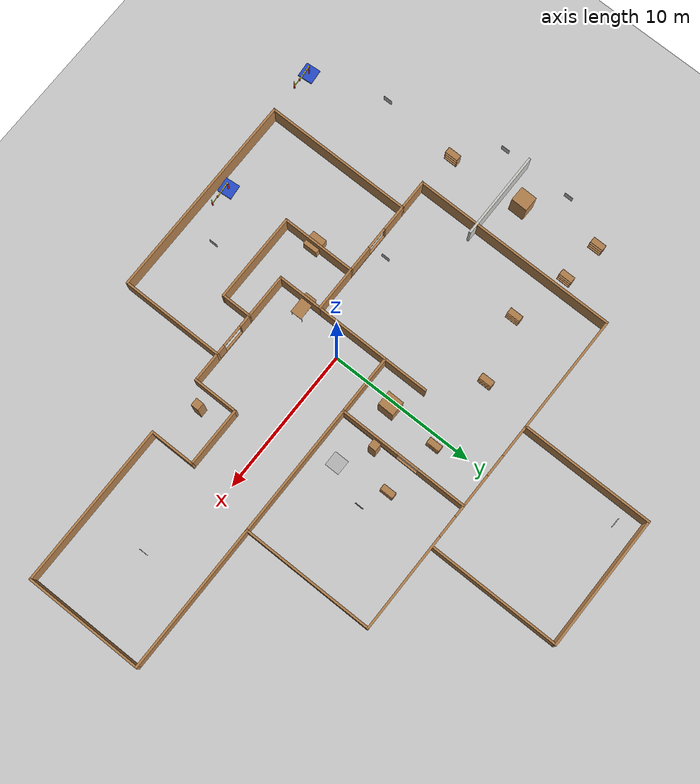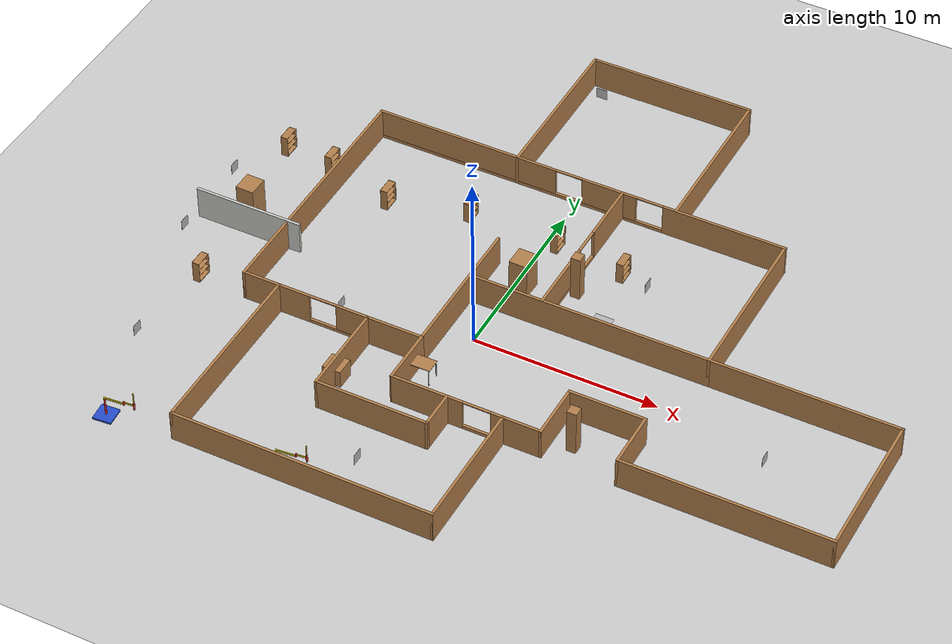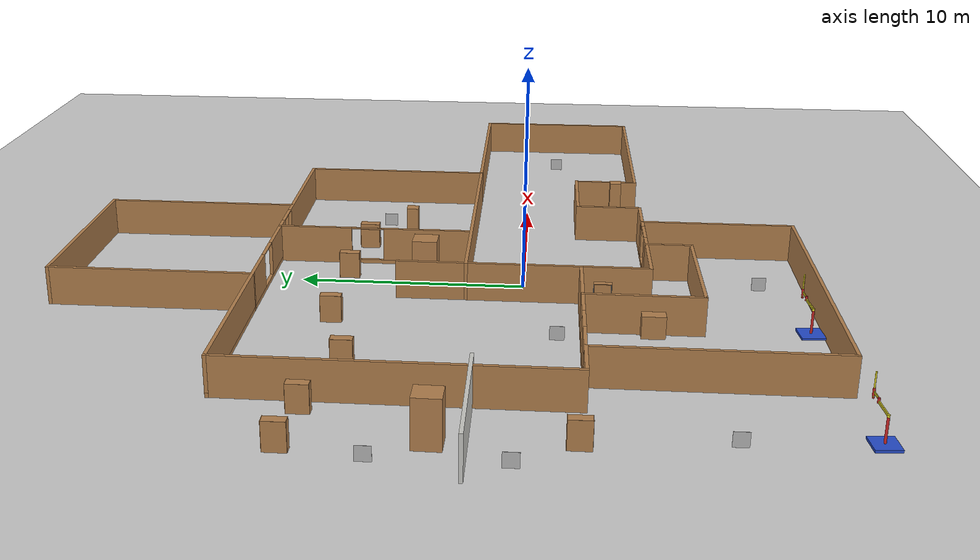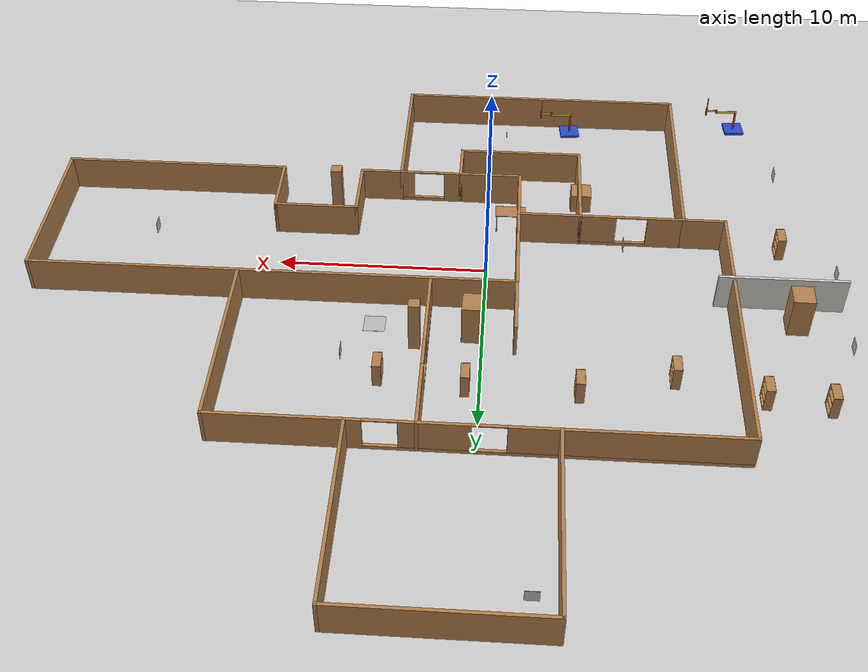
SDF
<sdf version="1.7">
 <world name="default">
  <light name="sun" type="directional">
   <pose>0 0 10 0 -0 0</pose>
   <diffuse>0.8 0.8 0.8 1</diffuse>
   <specular>0.2 0.2 0.2 1</specular>
   <attenuation>
    <range>1000</range>
    <constant>0.9</constant>
    <linear>0.01</linear>
    <quadratic>0.001</quadratic>
   </attenuation>
   <direction>-0.5 0.1 -0.9</direction>
   <spot><inner_angle>0</inner_angle><outer_angle>0</outer_angle><falloff>0</falloff></spot>
  </light>
  <model name="ground_plane">
   <static>1</static>
   <link name="link">
    <collision name="collision">
     <geometry><plane><normal>0 0 1</normal><size>25 25</size></plane></geometry>
     <surface><friction><ode><mu>100</mu><mu2>50</mu2></ode></friction></surface>
    </collision>
    <visual name="visual">
     <cast_shadows>0</cast_shadows>
     <geometry><plane><normal>0 0 1</normal><size>25 25</size></plane></geometry>
     <material>
      <script><uri>file://media/materials/scripts/gazebo.material</uri><name>Gazebo/Grey</name></script>
     </material>
    </visual>
   </link>
  </model>
  <gravity>0 0 -9.8</gravity>
  <magnetic_field>6e-06 2.3e-05 -4.2e-05</magnetic_field>
  <atmosphere type="adiabatic"/>
  <plugin name="ros_interface_plugin" filename="librotors_gazebo_ros_interface_plugin.so"/>
  <physics name="default_physics" default="0" type="ode">
   <max_step_size>0.001</max_step_size>
   <real_time_factor>1</real_time_factor>
   <real_time_update_rate>1000</real_time_update_rate>
  </physics>
  <scene>
   <sky><clouds><speed>30</speed></clouds><sunrise>5</sunrise><time>10</time><sunset>15</sunset></sky>
   <ambient>0.5 0.5 0.5 1</ambient>
   <background>0.7 0.7 0.7 1</background>
   <shadows>1</shadows>
  </scene>
  <spherical_coordinates>
   <surface_model>EARTH_WGS84</surface_model>
   <latitude_deg>0</latitude_deg>
   <longitude_deg>0</longitude_deg>
   <elevation>0</elevation>
   <heading_deg>0</heading_deg>
  </spherical_coordinates>
  <model name="table">
   <static>0</static>
   <link name="link">
    <collision name="surface">
     <pose>0 0 1 0 -0 0</pose>
     <geometry><box><size>1.5 0.8 0.03</size></box></geometry>
     <surface><friction><ode><mu>0.6</mu><mu2>0.6</mu2></ode></friction></surface>
    </collision>
    <visual name="visual1">
     <pose>0 0 1 0 -0 0</pose>
     <geometry><box><size>1.5 0.8 0.03</size></box></geometry>
     <material>
      <script><uri>file://media/materials/scripts/gazebo.material</uri><name>Gazebo/Wood</name></script>
     </material>
    </visual>
    <collision name="front_left_leg">
     <pose>0.68 0.38 0.5 0 -0 0</pose>
     <geometry><cylinder><radius>0.02</radius><length>1</length></cylinder></geometry>
    </collision>
    <visual name="front_left_leg">
     <pose>0.68 0.38 0.5 0 -0 0</pose>
     <geometry><cylinder><radius>0.02</radius><length>1</length></cylinder></geometry>
     <material>
      <script><uri>file://media/materials/scripts/gazebo.material</uri><name>Gazebo/Grey</name></script>
     </material>
    </visual>
    <collision name="front_right_leg">
     <pose>0.68 -0.38 0.5 0 -0 0</pose>
     <geometry><cylinder><radius>0.02</radius><length>1</length></cylinder></geometry>
    </collision>
    <visual name="front_right_leg">
     <pose>0.68 -0.38 0.5 0 -0 0</pose>
     <geometry><cylinder><radius>0.02</radius><length>1</length></cylinder></geometry>
     <material>
      <script><uri>file://media/materials/scripts/gazebo.material</uri><name>Gazebo/Grey</name></script>
     </material>
    </visual>
    <collision name="back_right_leg">
     <pose>-0.68 -0.38 0.5 0 -0 0</pose>
     <geometry><cylinder><radius>0.02</radius><length>1</length></cylinder></geometry>
    </collision>
    <visual name="back_right_leg">
     <pose>-0.68 -0.38 0.5 0 -0 0</pose>
     <geometry><cylinder><radius>0.02</radius><length>1</length></cylinder></geometry>
     <material>
      <script><uri>file://media/materials/scripts/gazebo.material</uri><name>Gazebo/Grey</name></script>
     </material>
    </visual>
    <collision name="back_left_leg">
     <pose>-0.68 0.38 0.5 0 -0 0</pose>
     <geometry><cylinder><radius>0.02</radius><length>1</length></cylinder></geometry>
    </collision>
    <visual name="back_left_leg">
     <pose>-0.68 0.38 0.5 0 -0 0</pose>
     <geometry><cylinder><radius>0.02</radius><length>1</length></cylinder></geometry>
     <material>
      <script><uri>file://media/materials/scripts/gazebo.material</uri><name>Gazebo/Grey</name></script>
     </material>
    </visual>
    <inertial>
     <inertia><ixx>1</ixx><ixy>0</ixy><ixz>0</ixz><iyy>1</iyy><iyz>0</iyz><izz>1</izz></inertia>
     <mass>1</mass>
    </inertial>
   </link>
   <pose>-1.09974 -3.44005 -2e-06 0 -4e-06 0.009466</pose>
  </model>
  <model name="unit_box_0_clone_0">
   <pose>3.05307 5.27266 1.29125 0 2e-06 0.001086</pose>
   <link name="link">
    <inertial>
     <mass>1</mass>
     <inertia>
      <ixx>0.166667</ixx>
      <ixy>0</ixy>
      <ixz>0</ixz>
      <iyy>0.166667</iyy>
      <iyz>0</iyz>
      <izz>0.166667</izz>
     </inertia>
    </inertial>
    <collision name="collision"><geometry><box><size>0.52404 0.528614 2.5825</size></box></geometry></collision>
    <visual name="visual">
     <geometry><box><size>0.52404 0.528614 2.5825</size></box></geometry>
     <material>
      <script><uri>file://media/materials/scripts/gazebo.material</uri><name>Gazebo/Wood</name></script>
     </material>
    </visual>
   </link>
   <static>0</static>
  </model>
  <model name="unit_box_0_clone_3">
   <pose>7.64627 -4.34048 1.29125 0 1e-06 0.000236</pose>
   <link name="link">
    <inertial>
     <mass>1</mass>
     <inertia>
      <ixx>0.166667</ixx>
      <ixy>0</ixy>
      <ixz>0</ixz>
      <iyy>0.166667</iyy>
      <iyz>0</iyz>
      <izz>0.166667</izz>
     </inertia>
    </inertial>
    <collision name="collision"><geometry><box><size>0.52404 0.528614 2.5825</size></box></geometry></collision>
    <visual name="visual">
     <geometry><box><size>0.52404 0.528614 2.5825</size></box></geometry>
     <material>
      <script><uri>file://media/materials/scripts/gazebo.material</uri><name>Gazebo/Wood</name></script>
     </material>
    </visual>
   </link>
   <static>0</static>
  </model>
  <model name="static_apriltag_0">
   <link name="link">
    <pose>0 0 0 0 1.57 0</pose>
    <inertial>
     <mass>0.39</mass>
     <inertia><ixx>0.00058</ixx><ixy>0</ixy><ixz>0</ixz><iyy>0.00058</iyy><iyz>0</iyz><izz>0.00019</izz></inertia>
    </inertial>
    <collision name="collision"><geometry><box><size>0.6 0.6 0.01</size></box></geometry></collision>
    <visual name="visual">
     <geometry><box><size>0.6 0.6 0.01</size></box></geometry>
     <material>
      <script>
       <uri>model://apriltag/materials/scripts</uri>
       <uri>model://apriltag/materials/textures</uri>
       <name>apriltag/Diffuse0</name>
      </script>
     </material>
    </visual>
    <gravity>0</gravity>
   </link>
   <pose>6.2472 6.68386 0.800731 3.1408 -0.000797 -3.14159</pose>
   <static>1</static>
   <pose>1.90787 0.108649 0 0 -0 0</pose>
  </model>
  <model name="static_apriltag_1">
   <link name="link">
    <pose>0 0 0 0 1.57 0</pose>
    <inertial>
     <mass>0.39</mass>
     <inertia><ixx>0.00058</ixx><ixy>0</ixy><ixz>0</ixz><iyy>0.00058</iyy><iyz>0</iyz><izz>0.00019</izz></inertia>
    </inertial>
    <collision name="collision"><geometry><box><size>0.6 0.6 0.01</size></box></geometry></collision>
    <visual name="visual">
     <geometry><box><size>0.6 0.6 0.01</size></box></geometry>
     <material>
      <script>
       <uri>model://apriltag/materials/scripts</uri>
       <uri>model://apriltag/materials/textures</uri>
       <name>apriltag/Diffuse1</name>
      </script>
     </material>
    </visual>
    <gravity>0</gravity>
   </link>
   <pose>-2.37496 19.0629 0.800899 0.000796 0.000796 1.57</pose>
   <static>1</static>
   <pose>1.36256 0.459264 0 0 -0 0</pose>
  </model>
  <model name="static_apriltag_2">
   <link name="link">
    <pose>0 0 0 0 1.57 0</pose>
    <inertial>
     <mass>0.39</mass>
     <inertia><ixx>0.00058</ixx><ixy>0</ixy><ixz>0</ixz><iyy>0.00058</iyy><iyz>0</iyz><izz>0.00019</izz></inertia>
    </inertial>
    <collision name="collision"><geometry><box><size>0.6 0.6 0.01</size></box></geometry></collision>
    <visual name="visual">
     <geometry><box><size>0.6 0.6 0.01</size></box></geometry>
     <material>
      <script>
       <uri>model://apriltag/materials/scripts</uri>
       <uri>model://apriltag/materials/textures</uri>
       <name>apriltag/Diffuse2</name>
      </script>
     </material>
    </visual>
    <gravity>0</gravity>
   </link>
   <pose>-16.5929 4.92565 0.800534 -0.000796 0.000796 -1e-06</pose>
   <static>1</static>
   <pose>0.80811 0.829943 0 0 -0 0</pose>
  </model>
  <model name="static_apriltag_3">
   <link name="link">
    <pose>0 0 0 -1.57 1.57 -0</pose>
    <inertial>
     <mass>0.39</mass>
     <inertia><ixx>0.00058</ixx><ixy>0</ixy><ixz>0</ixz><iyy>0.00058</iyy><iyz>0</iyz><izz>0.00019</izz></inertia>
    </inertial>
    <collision name="collision"><geometry><box><size>0.6 0.6 0.01</size></box></geometry></collision>
    <visual name="visual">
     <geometry><box><size>0.6 0.6 0.01</size></box></geometry>
     <material>
      <script>
       <uri>model://apriltag/materials/scripts</uri>
       <uri>model://apriltag/materials/textures</uri>
       <name>apriltag/Diffuse3</name>
      </script>
     </material>
    </visual>
    <gravity>0</gravity>
   </link>
   <pose>-6.59048 -1.46342 0.801382 1e-06 0.001593 1.57319</pose>
   <static>1</static>
   <pose>3.65849 3.02317 0 0 -0 0</pose>
  </model>
  <model name="static_apriltag_4">
   <link name="link">
    <pose>0 0 0 0 1.57 0</pose>
    <inertial>
     <mass>0.39</mass>
     <inertia><ixx>0.00058</ixx><ixy>0</ixy><ixz>0</ixz><iyy>0.00058</iyy><iyz>0</iyz><izz>0.00019</izz></inertia>
    </inertial>
    <collision name="collision"><geometry><box><size>0.6 0.6 0.01</size></box></geometry></collision>
    <visual name="visual">
     <geometry><box><size>0.6 0.6 0.01</size></box></geometry>
     <material>
      <script>
       <uri>model://apriltag/materials/scripts</uri>
       <uri>model://apriltag/materials/textures</uri>
       <name>apriltag/Diffuse4</name>
      </script>
     </material>
    </visual>
    <gravity>0</gravity>
   </link>
   <pose>16.248 -1.50157 0.8 -1.5708 -0.000796 3.14</pose>
   <static>1</static>
   <pose>3.93537 3.29316 0 0 -0 0</pose>
  </model>
  <model name="static_apriltag_5">
   <link name="link">
    <pose>0 0 0 -1.57 1.57 -0</pose>
    <inertial>
     <mass>0.39</mass>
     <inertia><ixx>0.00058</ixx><ixy>0</ixy><ixz>0</ixz><iyy>0.00058</iyy><iyz>0</iyz><izz>0.00019</izz></inertia>
    </inertial>
    <collision name="collision"><geometry><box><size>0.6 0.6 0.01</size></box></geometry></collision>
    <visual name="visual">
     <geometry><box><size>0.6 0.6 0.01</size></box></geometry>
     <material>
      <script>
       <uri>model://apriltag/materials/scripts</uri>
       <uri>model://apriltag/materials/textures</uri>
       <name>apriltag/Diffuse5</name>
      </script>
     </material>
    </visual>
    <gravity>0</gravity>
   </link>
   <pose>-0.752387 -10.2182 0.800977 3.14159 -0.001593 1.57159</pose>
   <static>1</static>
   <pose>5.04082 3.71574 0 0 -0 0</pose>
  </model>
  <model name="static_apriltag_6">
   <link name="link">
    <pose>0 0 0 -1.57 1.57 -0</pose>
    <inertial>
     <mass>0.39</mass>
     <inertia><ixx>0.00058</ixx><ixy>0</ixy><ixz>0</ixz><iyy>0.00058</iyy><iyz>0</iyz><izz>0.00019</izz></inertia>
    </inertial>
    <collision name="collision"><geometry><box><size>0.6 0.6 0.01</size></box></geometry></collision>
    <visual name="visual">
     <geometry><box><size>0.6 0.6 0.01</size></box></geometry>
     <material>
      <script>
       <uri>model://apriltag/materials/scripts</uri>
       <uri>model://apriltag/materials/textures</uri>
       <name>apriltag/Diffuse6</name>
      </script>
     </material>
    </visual>
    <gravity>0</gravity>
   </link>
   <pose>-14.5922 -7.60274 0.8 0 0 -1.57</pose>
   <static>1</static>
   <pose>3.43144 4.34187 0 0 -0 0</pose>
  </model>
  <model name="static_apriltag_7">
   <link name="link">
    <pose>0 0 0 0 1.57 0</pose>
    <inertial>
     <mass>0.39</mass>
     <inertia><ixx>0.00058</ixx><ixy>0</ixy><ixz>0</ixz><iyy>0.00058</iyy><iyz>0</iyz><izz>0.00019</izz></inertia>
    </inertial>
    <collision name="collision"><geometry><box><size>0.6 0.6 0.01</size></box></geometry></collision>
    <visual name="visual">
     <geometry><box><size>0.6 0.6 0.01</size></box></geometry>
     <material>
      <script>
       <uri>model://apriltag/materials/scripts</uri>
       <uri>model://apriltag/materials/textures</uri>
       <name>apriltag/Diffuse7</name>
      </script>
     </material>
    </visual>
    <gravity>0</gravity>
   </link>
   <pose>-16.5926 0.054368 0.800661 -0.000796 0.000796 -1e-06</pose>
   <static>1</static>
   <pose>3.12393 4.47604 0 0 -0 0</pose>
  </model>
  <model name="0810_MAP2_elment_1">
   <pose>5 4 -0.115 0 -0 0</pose>
   <link name="startflag">
    <pose>0 0 0.115 0 -0 0</pose>
    <inertial>
     <mass>0.39</mass>
     <inertia><ixx>0.00058</ixx><ixy>0</ixy><ixz>0</ixz><iyy>0.00058</iyy><iyz>0</iyz><izz>0.00019</izz></inertia>
    </inertial>
    <collision name="collision"><geometry><box><size>1 1 0.01</size></box></geometry></collision>
    <visual name="visual">
     <geometry><box><size>1 1 0.01</size></box></geometry>
     <material>
      <script>
       <uri>model://apriltag/materials/scripts</uri>
       <uri>model://apriltag/materials/textures</uri>
       <name>startflag/Diffuse</name>
      </script>
     </material>
    </visual>
   </link>
   <link name="Wall_0">
    <collision name="Wall_0_Collision">
     <geometry><box><size>13.15 0.15 1.8</size></box></geometry>
     <pose>0 0 0.9 0 -0 0</pose>
    </collision>
    <visual name="Wall_0_Visual">
     <pose>0 0 0.9 0 -0 0</pose>
     <geometry><box><size>13.15 0.15 1.8</size></box></geometry>
     <material>
      <script><uri>file://media/materials/scripts/gazebo.material</uri><name>Gazebo/Wood</name></script>
      <ambient>1 1 1 1</ambient>
     </material>
     <meta><layer>0</layer></meta>
    </visual>
    <pose>0 -1.5 0 0 -0 0</pose>
   </link>
   <link name="Wall_10">
    <collision name="Wall_10_Collision">
     <geometry><box><size>14.15 0.15 1.8</size></box></geometry>
     <pose>0 0 0.9 0 -0 0</pose>
    </collision>
    <visual name="Wall_10_Visual">
     <pose>0 0 0.9 0 -0 0</pose>
     <geometry><box><size>14.15 0.15 1.8</size></box></geometry>
     <material>
      <script><uri>file://media/materials/scripts/gazebo.material</uri><name>Gazebo/Wood</name></script>
      <ambient>1 1 1 1</ambient>
     </material>
     <meta><layer>0</layer></meta>
    </visual>
    <pose>-16.5 0.5 0 0 -0 -1.5708</pose>
   </link>
   <link name="Wall_14">
    <collision name="Wall_14_Collision">
     <geometry><box><size>5.15 0.15 1.8</size></box></geometry>
     <pose>0 0 0.9 0 -0 0</pose>
    </collision>
    <visual name="Wall_14_Visual">
     <pose>0 0 0.9 0 -0 0</pose>
     <geometry><box><size>5.15 0.15 1.8</size></box></geometry>
     <material>
      <script><uri>file://media/materials/scripts/gazebo.material</uri><name>Gazebo/Wood</name></script>
      <ambient>1 1 1 1</ambient>
     </material>
     <meta><layer>0</layer></meta>
    </visual>
    <pose>-6.5 -4 0 0 -0 -1.5708</pose>
   </link>
   <link name="Wall_16">
    <collision name="Wall_16_Collision">
     <geometry><box><size>10.15 0.15 1.8</size></box></geometry>
     <pose>0 0 0.9 0 -0 0</pose>
    </collision>
    <visual name="Wall_16_Visual">
     <pose>0 0 0.9 0 -0 0</pose>
     <geometry><box><size>10.15 0.15 1.8</size></box></geometry>
     <material>
      <script><uri>file://media/materials/scripts/gazebo.material</uri><name>Gazebo/Wood</name></script>
      <ambient>1 1 1 1</ambient>
     </material>
     <meta><layer>0</layer></meta>
    </visual>
    <pose>-14.5 -11.5 0 0 -0 -1.5708</pose>
   </link>
   <link name="Wall_18">
    <collision name="Wall_18_Collision">
     <geometry><box><size>3.15 0.15 1.8</size></box></geometry>
     <pose>0 0 0.9 0 -0 0</pose>
    </collision>
    <visual name="Wall_18_Visual">
     <pose>0 0 0.9 0 -0 0</pose>
     <geometry><box><size>3.15 0.15 1.8</size></box></geometry>
     <material>
      <script><uri>file://media/materials/scripts/gazebo.material</uri><name>Gazebo/Wood</name></script>
      <ambient>1 1 1 1</ambient>
     </material>
     <meta><layer>0</layer></meta>
    </visual>
    <pose>-6.5 -8 0 0 -0 -1.5708</pose>
   </link>
   <link name="Wall_2">
    <collision name="Wall_2_Collision">
     <geometry><box><size>9.15 0.15 1.8</size></box></geometry>
     <pose>0 0 0.9 0 -0 0</pose>
    </collision>
    <visual name="Wall_2_Visual">
     <pose>0 0 0.9 0 -0 0</pose>
     <geometry><box><size>9.15 0.15 1.8</size></box></geometry>
     <material>
      <script><uri>file://media/materials/scripts/gazebo.material</uri><name>Gazebo/Wood</name></script>
      <ambient>1 1 1 1</ambient>
     </material>
     <meta><layer>0</layer></meta>
    </visual>
    <pose>6.5 3 0 0 -0 1.5708</pose>
   </link>
   <link name="Wall_20">
    <collision name="Wall_20_Collision">
     <geometry><box><size>5.15 0.15 1.8</size></box></geometry>
     <pose>0 0 0.9 0 -0 0</pose>
    </collision>
    <visual name="Wall_20_Visual">
     <pose>0 0 0.9 0 -0 0</pose>
     <geometry><box><size>5.15 0.15 1.8</size></box></geometry>
     <material>
      <script><uri>file://media/materials/scripts/gazebo.material</uri><name>Gazebo/Wood</name></script>
      <ambient>1 1 1 1</ambient>
     </material>
     <meta><layer>0</layer></meta>
    </visual>
    <pose>-9.5 -9 0 0 -0 -1.5708</pose>
   </link>
   <link name="Wall_22">
    <collision name="Wall_22_Collision">
     <geometry><box><size>2.15 0.15 1.8</size></box></geometry>
     <pose>0 0 0.9 0 -0 0</pose>
    </collision>
    <visual name="Wall_22_Visual">
     <pose>0 0 0.9 0 -0 0</pose>
     <geometry><box><size>2.15 0.15 1.8</size></box></geometry>
     <material>
      <script><uri>file://media/materials/scripts/gazebo.material</uri><name>Gazebo/Wood</name></script>
      <ambient>1 1 1 1</ambient>
     </material>
     <meta><layer>0</layer></meta>
    </visual>
    <pose>-15.5 -6.5 0 0 -0 0</pose>
   </link>
   <link name="Wall_24">
    <collision name="Wall_24_Collision">
     <geometry><box><size>3.15 0.15 1.8</size></box></geometry>
     <pose>0 0 0.9 0 -0 0</pose>
    </collision>
    <visual name="Wall_24_Visual">
     <pose>0 0 0.9 0 -0 0</pose>
     <geometry><box><size>3.15 0.15 1.8</size></box></geometry>
     <material>
      <script><uri>file://media/materials/scripts/gazebo.material</uri><name>Gazebo/Wood</name></script>
      <ambient>1 1 1 1</ambient>
     </material>
     <meta><layer>0</layer></meta>
    </visual>
    <pose>-8 -6.5 0 0 -0 0</pose>
   </link>
   <link name="Wall_26">
    <collision name="Wall_26_Collision">
     <geometry><box><size>14.15 0.15 1.8</size></box></geometry>
     <pose>0 0 0.9 0 -0 0</pose>
    </collision>
    <visual name="Wall_26_Visual">
     <pose>0 0 0.9 0 -0 0</pose>
     <geometry><box><size>14.15 0.15 1.8</size></box></geometry>
     <material>
      <script><uri>file://media/materials/scripts/gazebo.material</uri><name>Gazebo/Wood</name></script>
      <ambient>1 1 1 1</ambient>
     </material>
     <meta><layer>0</layer></meta>
    </visual>
    <pose>-7.5 -16.5 0 0 -0 0</pose>
   </link>
   <link name="Wall_28">
    <collision name="Wall_28_Collision">
     <geometry><box><size>6.15 0.15 1.8</size></box></geometry>
     <pose>0 0 0.9 0 -0 0</pose>
    </collision>
    <visual name="Wall_28_Visual">
     <pose>0 0 0.9 0 -0 0</pose>
     <geometry><box><size>6.15 0.15 1.8</size></box></geometry>
     <material>
      <script><uri>file://media/materials/scripts/gazebo.material</uri><name>Gazebo/Wood</name></script>
      <ambient>1 1 1 1</ambient>
     </material>
     <meta><layer>0</layer></meta>
    </visual>
    <pose>-6.5 -11.5 0 0 -0 0</pose>
   </link>
   <link name="Wall_30">
    <collision name="Wall_30_Collision">
     <geometry><box><size>2.15 0.15 1.8</size></box></geometry>
     <pose>0 0 0.9 0 -0 0</pose>
    </collision>
    <visual name="Wall_30_Visual">
     <pose>0 0 0.9 0 -0 0</pose>
     <geometry><box><size>2.15 0.15 1.8</size></box></geometry>
     <material>
      <script><uri>file://media/materials/scripts/gazebo.material</uri><name>Gazebo/Wood</name></script>
      <ambient>1 1 1 1</ambient>
     </material>
     <meta><layer>0</layer></meta>
    </visual>
    <pose>-3.5 -10.5 0 0 -0 -1.5708</pose>
   </link>
   <link name="Wall_32">
    <collision name="Wall_32_Collision">
     <geometry><box><size>7.15 0.15 1.8</size></box></geometry>
     <pose>0 0 0.9 0 -0 0</pose>
    </collision>
    <visual name="Wall_32_Visual">
     <pose>0 0 0.9 0 -0 0</pose>
     <geometry><box><size>7.15 0.15 1.8</size></box></geometry>
     <material>
      <script><uri>file://media/materials/scripts/gazebo.material</uri><name>Gazebo/Wood</name></script>
      <ambient>1 1 1 1</ambient>
     </material>
     <meta><layer>0</layer></meta>
    </visual>
    <pose>-0.5 -13 0 0 -0 1.5708</pose>
   </link>
   <link name="Wall_36">
    <collision name="Wall_36_Collision">
     <geometry><box><size>3.15 0.15 1.8</size></box></geometry>
     <pose>0 0 0.9 0 -0 0</pose>
    </collision>
    <visual name="Wall_36_Visual">
     <pose>0 0 0.9 0 -0 0</pose>
     <geometry><box><size>3.15 0.15 1.8</size></box></geometry>
     <material>
      <script><uri>file://media/materials/scripts/gazebo.material</uri><name>Gazebo/Wood</name></script>
      <ambient>1 1 1 1</ambient>
     </material>
     <meta><layer>0</layer></meta>
    </visual>
    <pose>-5 -9.5 0 0 -0 0</pose>
   </link>
   <link name="Wall_37">
    <pose>-2 -9.5 0 0 -0 0</pose>
    <visual name="Wall_37_Visual_0">
     <pose>-1.11242 0 0.9 0 -0 0</pose>
     <geometry><box><size>0.925162 0.15 1.8</size></box></geometry>
     <material>
      <script><uri>file://media/materials/scripts/gazebo.material</uri><name>Gazebo/Wood</name></script>
      <ambient>1 1 1 1</ambient>
     </material>
     <meta><layer>0</layer></meta>
    </visual>
    <collision name="Wall_37_Collision_0">
     <geometry><box><size>0.925162 0.15 1.8</size></box></geometry>
     <pose>-1.11242 0 0.9 0 -0 0</pose>
    </collision>
    <visual name="Wall_37_Visual_1">
     <pose>0.462581 0 0.125 0 -0 0</pose>
     <geometry><box><size>2.22484 0.15 0.25</size></box></geometry>
     <material>
      <script><uri>file://media/materials/scripts/gazebo.material</uri><name>Gazebo/Wood</name></script>
      <ambient>1 1 1 1</ambient>
     </material>
     <meta><layer>0</layer></meta>
    </visual>
    <collision name="Wall_37_Collision_1">
     <geometry><box><size>2.22484 0.15 0.25</size></box></geometry>
     <pose>0.462581 0 0.125 0 -0 0</pose>
    </collision>
    <visual name="Wall_37_Visual_2">
     <pose>1.21258 0 1.025 0 -0 0</pose>
     <geometry><box><size>0.724838 0.15 1.55</size></box></geometry>
     <material>
      <script><uri>file://media/materials/scripts/gazebo.material</uri><name>Gazebo/Wood</name></script>
      <ambient>1 1 1 1</ambient>
     </material>
     <meta><layer>0</layer></meta>
    </visual>
    <collision name="Wall_37_Collision_2">
     <geometry><box><size>0.724838 0.15 1.55</size></box></geometry>
     <pose>1.21258 0 1.025 0 -0 0</pose>
    </collision>
    <visual name="Wall_37_Visual_3">
     <pose>0.100162 0 1.775 0 -0 0</pose>
     <geometry><box><size>1.5 0.15 0.05</size></box></geometry>
     <material>
      <script><uri>file://media/materials/scripts/gazebo.material</uri><name>Gazebo/Wood</name></script>
      <ambient>1 1 1 1</ambient>
     </material>
     <meta><layer>0</layer></meta>
    </visual>
    <collision name="Wall_37_Collision_3">
     <geometry><box><size>1.5 0.15 0.05</size></box></geometry>
     <pose>0.100162 0 1.775 0 -0 0</pose>
    </collision>
   </link>
   <link name="Wall_39">
    <pose>-12 -6.5 0 0 -0 0</pose>
    <visual name="Wall_39_Visual_0">
     <pose>-1.66475 0 0.9 0 -0 0</pose>
     <geometry><box><size>1.82051 0.15 1.8</size></box></geometry>
     <material>
      <script><uri>file://media/materials/scripts/gazebo.material</uri><name>Gazebo/Wood</name></script>
      <ambient>1 1 1 1</ambient>
     </material>
     <meta><layer>0</layer></meta>
    </visual>
    <collision name="Wall_39_Collision_0">
     <geometry><box><size>1.82051 0.15 1.8</size></box></geometry>
     <pose>-1.66475 0 0.9 0 -0 0</pose>
    </collision>
    <visual name="Wall_39_Visual_1">
     <pose>0.910253 0 0.125 0 -0 0</pose>
     <geometry><box><size>3.3295 0.15 0.25</size></box></geometry>
     <material>
      <script><uri>file://media/materials/scripts/gazebo.material</uri><name>Gazebo/Wood</name></script>
      <ambient>1 1 1 1</ambient>
     </material>
     <meta><layer>0</layer></meta>
    </visual>
    <collision name="Wall_39_Collision_1">
     <geometry><box><size>3.3295 0.15 0.25</size></box></geometry>
     <pose>0.910253 0 0.125 0 -0 0</pose>
    </collision>
    <visual name="Wall_39_Visual_2">
     <pose>1.66025 0 1.025 0 -0 0</pose>
     <geometry><box><size>1.8295 0.15 1.55</size></box></geometry>
     <material>
      <script><uri>file://media/materials/scripts/gazebo.material</uri><name>Gazebo/Wood</name></script>
      <ambient>1 1 1 1</ambient>
     </material>
     <meta><layer>0</layer></meta>
    </visual>
    <collision name="Wall_39_Collision_2">
     <geometry><box><size>1.8295 0.15 1.55</size></box></geometry>
     <pose>1.66025 0 1.025 0 -0 0</pose>
    </collision>
    <visual name="Wall_39_Visual_3">
     <pose>-0.004495 0 1.775 0 -0 0</pose>
     <geometry><box><size>1.5 0.15 0.05</size></box></geometry>
     <material>
      <script><uri>file://media/materials/scripts/gazebo.material</uri><name>Gazebo/Wood</name></script>
      <ambient>1 1 1 1</ambient>
     </material>
     <meta><layer>0</layer></meta>
    </visual>
    <collision name="Wall_39_Collision_3">
     <geometry><box><size>1.5 0.15 0.05</size></box></geometry>
     <pose>-0.004495 0 1.775 0 -0 0</pose>
    </collision>
   </link>
   <link name="Wall_4">
    <pose>-5 7.5 0 0 -0 3.14159</pose>
    <visual name="Wall_4_Visual_0">
     <pose>-8.17816 0 0.9 0 -0 0</pose>
     <geometry><box><size>6.79369 0.15 1.8</size></box></geometry>
     <material>
      <script><uri>file://media/materials/scripts/gazebo.material</uri><name>Gazebo/Wood</name></script>
      <ambient>1 1 1 1</ambient>
     </material>
     <meta><layer>0</layer></meta>
    </visual>
    <collision name="Wall_4_Collision_0">
     <geometry><box><size>6.79369 0.15 1.8</size></box></geometry>
     <pose>-8.17816 0 0.9 0 -0 0</pose>
    </collision>
    <visual name="Wall_4_Visual_1">
     <pose>3.39684 0 0.125 0 -0 0</pose>
     <geometry><box><size>16.3563 0.15 0.25</size></box></geometry>
     <material>
      <script><uri>file://media/materials/scripts/gazebo.material</uri><name>Gazebo/Wood</name></script>
      <ambient>1 1 1 1</ambient>
     </material>
     <meta><layer>0</layer></meta>
    </visual>
    <collision name="Wall_4_Collision_1">
     <geometry><box><size>16.3563 0.15 0.25</size></box></geometry>
     <pose>3.39684 0 0.125 0 -0 0</pose>
    </collision>
    <visual name="Wall_4_Visual_2">
     <pose>-1.75236 0 1.025 0 -0 0</pose>
     <geometry><box><size>3.0579 0.15 1.55</size></box></geometry>
     <material>
      <script><uri>file://media/materials/scripts/gazebo.material</uri><name>Gazebo/Wood</name></script>
      <ambient>1 1 1 1</ambient>
     </material>
     <meta><layer>0</layer></meta>
    </visual>
    <collision name="Wall_4_Collision_2">
     <geometry><box><size>3.0579 0.15 1.55</size></box></geometry>
     <pose>-1.75236 0 1.025 0 -0 0</pose>
    </collision>
    <visual name="Wall_4_Visual_3">
     <pose>6.4258 0 1.025 0 -0 0</pose>
     <geometry><box><size>10.2984 0.15 1.55</size></box></geometry>
     <material>
      <script><uri>file://media/materials/scripts/gazebo.material</uri><name>Gazebo/Wood</name></script>
      <ambient>1 1 1 1</ambient>
     </material>
     <meta><layer>0</layer></meta>
    </visual>
    <collision name="Wall_4_Collision_3">
     <geometry><box><size>10.2984 0.15 1.55</size></box></geometry>
     <pose>6.4258 0 1.025 0 -0 0</pose>
    </collision>
    <visual name="Wall_4_Visual_4">
     <pose>-4.03131 0 1.775 0 -0 0</pose>
     <geometry><box><size>1.5 0.15 0.05</size></box></geometry>
     <material>
      <script><uri>file://media/materials/scripts/gazebo.material</uri><name>Gazebo/Wood</name></script>
      <ambient>1 1 1 1</ambient>
     </material>
     <meta><layer>0</layer></meta>
    </visual>
    <collision name="Wall_4_Collision_4">
     <geometry><box><size>1.5 0.15 0.05</size></box></geometry>
     <pose>-4.03131 0 1.775 0 -0 0</pose>
    </collision>
    <visual name="Wall_4_Visual_5">
     <pose>0.526593 0 1.775 0 -0 0</pose>
     <geometry><box><size>1.5 0.15 0.05</size></box></geometry>
     <material>
      <script><uri>file://media/materials/scripts/gazebo.material</uri><name>Gazebo/Wood</name></script>
      <ambient>1 1 1 1</ambient>
     </material>
     <meta><layer>0</layer></meta>
    </visual>
    <collision name="Wall_4_Collision_5">
     <geometry><box><size>1.5 0.15 0.05</size></box></geometry>
     <pose>0.526593 0 1.775 0 -0 0</pose>
    </collision>
   </link>
   <link name="Wall_41">
    <collision name="Wall_41_Collision">
     <geometry><box><size>3.15 0.15 1.8</size></box></geometry>
     <pose>0 0 0.9 0 -0 0</pose>
    </collision>
    <visual name="Wall_41_Visual">
     <pose>0 0 0.9 0 -0 0</pose>
     <geometry><box><size>3.15 0.15 1.8</size></box></geometry>
     <material>
      <script><uri>file://media/materials/scripts/gazebo.material</uri><name>Gazebo/Wood</name></script>
      <ambient>1 1 1 1</ambient>
     </material>
     <meta><layer>0</layer></meta>
    </visual>
    <pose>-6.5 0 0 0 -0 1.5708</pose>
   </link>
   <link name="Wall_43">
    <collision name="Wall_43_Collision">
     <geometry><box><size>2.15 0.15 1.8</size></box></geometry>
     <pose>0 0 0.9 0 -0 0</pose>
    </collision>
    <visual name="Wall_43_Visual">
     <pose>0 0 0.9 0 -0 0</pose>
     <geometry><box><size>2.15 0.15 1.8</size></box></geometry>
     <material>
      <script><uri>file://media/materials/scripts/gazebo.material</uri><name>Gazebo/Wood</name></script>
      <ambient>1 1 1 1</ambient>
     </material>
     <meta><layer>0</layer></meta>
    </visual>
    <pose>0.5 -9.5 0 0 -0 0</pose>
   </link>
   <link name="Wall_44">
    <collision name="Wall_44_Collision">
     <geometry><box><size>3.15 0.15 1.8</size></box></geometry>
     <pose>0 0 0.9 0 -0 0</pose>
    </collision>
    <visual name="Wall_44_Visual">
     <pose>0 0 0.9 0 -0 0</pose>
     <geometry><box><size>3.15 0.15 1.8</size></box></geometry>
     <material>
      <script><uri>file://media/materials/scripts/gazebo.material</uri><name>Gazebo/Wood</name></script>
      <ambient>1 1 1 1</ambient>
     </material>
     <meta><layer>0</layer></meta>
    </visual>
    <pose>1.5 -8 0 0 -0 1.5708</pose>
   </link>
   <link name="Wall_45">
    <collision name="Wall_45_Collision">
     <geometry><box><size>4.15 0.15 1.8</size></box></geometry>
     <pose>0 0 0.9 0 -0 0</pose>
    </collision>
    <visual name="Wall_45_Visual">
     <pose>0 0 0.9 0 -0 0</pose>
     <geometry><box><size>4.15 0.15 1.8</size></box></geometry>
     <material>
      <script><uri>file://media/materials/scripts/gazebo.material</uri><name>Gazebo/Wood</name></script>
      <ambient>1 1 1 1</ambient>
     </material>
     <meta><layer>0</layer></meta>
    </visual>
    <pose>3.5 -6.5 0 0 -0 0</pose>
   </link>
   <link name="Wall_46">
    <collision name="Wall_46_Collision">
     <geometry><box><size>3.15 0.15 1.8</size></box></geometry>
     <pose>0 0 0.9 0 -0 0</pose>
    </collision>
    <visual name="Wall_46_Visual">
     <pose>0 0 0.9 0 -0 0</pose>
     <geometry><box><size>3.15 0.15 1.8</size></box></geometry>
     <material>
      <script><uri>file://media/materials/scripts/gazebo.material</uri><name>Gazebo/Wood</name></script>
      <ambient>1 1 1 1</ambient>
     </material>
     <meta><layer>0</layer></meta>
    </visual>
    <pose>5.5 -8 0 0 -0 -1.5708</pose>
   </link>
   <link name="Wall_47">
    <collision name="Wall_47_Collision">
     <geometry><box><size>11.15 0.15 1.8</size></box></geometry>
     <pose>0 0 0.9 0 -0 0</pose>
    </collision>
    <visual name="Wall_47_Visual">
     <pose>0 0 0.9 0 -0 0</pose>
     <geometry><box><size>11.15 0.15 1.8</size></box></geometry>
     <material>
      <script><uri>file://media/materials/scripts/gazebo.material</uri><name>Gazebo/Wood</name></script>
      <ambient>1 1 1 1</ambient>
     </material>
     <meta><layer>0</layer></meta>
    </visual>
    <pose>11 -9.5 0 0 -0 0</pose>
   </link>
   <link name="Wall_48">
    <collision name="Wall_48_Collision">
     <geometry><box><size>8.15 0.15 1.8</size></box></geometry>
     <pose>0 0 0.9 0 -0 0</pose>
    </collision>
    <visual name="Wall_48_Visual">
     <pose>0 0 0.9 0 -0 0</pose>
     <geometry><box><size>8.15 0.15 1.8</size></box></geometry>
     <material>
      <script><uri>file://media/materials/scripts/gazebo.material</uri><name>Gazebo/Wood</name></script>
      <ambient>1 1 1 1</ambient>
     </material>
     <meta><layer>0</layer></meta>
    </visual>
    <pose>16.5 -5.5 0 0 -0 1.5708</pose>
   </link>
   <link name="Wall_49">
    <collision name="Wall_49_Collision">
     <geometry><box><size>10.15 0.15 1.8</size></box></geometry>
     <pose>0 0 0.9 0 -0 0</pose>
    </collision>
    <visual name="Wall_49_Visual">
     <pose>0 0 0.9 0 -0 0</pose>
     <geometry><box><size>10.15 0.15 1.8</size></box></geometry>
     <material>
      <script><uri>file://media/materials/scripts/gazebo.material</uri><name>Gazebo/Wood</name></script>
      <ambient>1 1 1 1</ambient>
     </material>
     <meta><layer>0</layer></meta>
    </visual>
    <pose>11.5 -1.5 0 0 -0 3.14159</pose>
   </link>
   <link name="Wall_54">
    <collision name="Wall_54_Collision">
     <geometry><box><size>9.15 0.15 1.8</size></box></geometry>
     <pose>0 0 0.9 0 -0 0</pose>
    </collision>
    <visual name="Wall_54_Visual">
     <pose>0 0 0.9 0 -0 0</pose>
     <geometry><box><size>9.15 0.15 1.8</size></box></geometry>
     <material>
      <script><uri>file://media/materials/scripts/gazebo.material</uri><name>Gazebo/Wood</name></script>
      <ambient>1 1 1 1</ambient>
     </material>
     <meta><layer>0</layer></meta>
    </visual>
    <pose>-4 16.5 0 0 -0 3.14159</pose>
   </link>
   <link name="Wall_57">
    <collision name="Wall_57_Collision">
     <geometry><box><size>9.15 0.15 1.8</size></box></geometry>
     <pose>0 0 0.9 0 -0 0</pose>
    </collision>
    <visual name="Wall_57_Visual">
     <pose>0 0 0.9 0 -0 0</pose>
     <geometry><box><size>9.15 0.15 1.8</size></box></geometry>
     <material>
      <script><uri>file://media/materials/scripts/gazebo.material</uri><name>Gazebo/Wood</name></script>
      <ambient>1 1 1 1</ambient>
     </material>
     <meta><layer>0</layer></meta>
    </visual>
    <pose>-8.5 12 0 0 -0 -1.5708</pose>
   </link>
   <link name="Wall_6">
    <pose>-2.5 3 0 0 -0 -1.5708</pose>
    <visual name="Wall_6_Visual_0">
     <pose>-2.84145 0 0.9 0 -0 0</pose>
     <geometry><box><size>3.46711 0.15 1.8</size></box></geometry>
     <material>
      <script><uri>file://media/materials/scripts/gazebo.material</uri><name>Gazebo/Wood</name></script>
      <ambient>1 1 1 1</ambient>
     </material>
     <meta><layer>0</layer></meta>
    </visual>
    <collision name="Wall_6_Collision_0">
     <geometry><box><size>3.46711 0.15 1.8</size></box></geometry>
     <pose>-2.84145 0 0.9 0 -0 0</pose>
    </collision>
    <visual name="Wall_6_Visual_1">
     <pose>1.73355 0 0.125 0 -0 0</pose>
     <geometry><box><size>5.68289 0.15 0.25</size></box></geometry>
     <material>
      <script><uri>file://media/materials/scripts/gazebo.material</uri><name>Gazebo/Wood</name></script>
      <ambient>1 1 1 1</ambient>
     </material>
     <meta><layer>0</layer></meta>
    </visual>
    <collision name="Wall_6_Collision_1">
     <geometry><box><size>5.68289 0.15 0.25</size></box></geometry>
     <pose>1.73355 0 0.125 0 -0 0</pose>
    </collision>
    <visual name="Wall_6_Visual_2">
     <pose>2.48355 0 1.025 0 -0 0</pose>
     <geometry><box><size>4.18289 0.15 1.55</size></box></geometry>
     <material>
      <script><uri>file://media/materials/scripts/gazebo.material</uri><name>Gazebo/Wood</name></script>
      <ambient>1 1 1 1</ambient>
     </material>
     <meta><layer>0</layer></meta>
    </visual>
    <collision name="Wall_6_Collision_2">
     <geometry><box><size>4.18289 0.15 1.55</size></box></geometry>
     <pose>2.48355 0 1.025 0 -0 0</pose>
    </collision>
    <visual name="Wall_6_Visual_3">
     <pose>-0.357894 0 1.775 0 -0 0</pose>
     <geometry><box><size>1.5 0.15 0.05</size></box></geometry>
     <material>
      <script><uri>file://media/materials/scripts/gazebo.material</uri><name>Gazebo/Wood</name></script>
      <ambient>1 1 1 1</ambient>
     </material>
     <meta><layer>0</layer></meta>
    </visual>
    <collision name="Wall_6_Collision_3">
     <geometry><box><size>1.5 0.15 0.05</size></box></geometry>
     <pose>-0.357894 0 1.775 0 -0 0</pose>
    </collision>
   </link>
   <link name="Wall_8">
    <collision name="Wall_8_Collision">
     <geometry><box><size>9.15 0.15 1.8</size></box></geometry>
     <pose>0 0 0.9 0 -0 0</pose>
    </collision>
    <visual name="Wall_8_Visual">
     <pose>0 0 0.9 0 -0 0</pose>
     <geometry><box><size>9.15 0.15 1.8</size></box></geometry>
     <material>
      <script><uri>file://media/materials/scripts/gazebo.material</uri><name>Gazebo/Wood</name></script>
      <ambient>1 1 1 1</ambient>
     </material>
     <meta><layer>0</layer></meta>
    </visual>
    <pose>0.5 12 0 0 -0 1.5708</pose>
   </link>
   <static>1</static>
  </model>
  <model name="bookshelf_clone">
   <static>1</static>
   <link name="link">
    <inertial><mass>1</mass></inertial>
    <collision name="back">
     <pose>0 0.005 0.6 0 -0 0</pose>
     <geometry><box><size>0.9 0.01 1.2</size></box></geometry>
    </collision>
    <visual name="visual1">
     <pose>0 0.005 0.6 0 -0 0</pose>
     <geometry><box><size>0.9 0.01 1.2</size></box></geometry>
     <material>
      <script><uri>file://media/materials/scripts/gazebo.material</uri><name>Gazebo/Wood</name></script>
     </material>
    </visual>
    <collision name="left_side">
     <pose>0.45 -0.195 0.6 0 -0 0</pose>
     <geometry><box><size>0.02 0.4 1.2</size></box></geometry>
    </collision>
    <visual name="visual2">
     <pose>0.45 -0.195 0.6 0 -0 0</pose>
     <geometry><box><size>0.02 0.4 1.2</size></box></geometry>
     <material>
      <script><uri>file://media/materials/scripts/gazebo.material</uri><name>Gazebo/Wood</name></script>
     </material>
    </visual>
    <collision name="right_side">
     <pose>-0.45 -0.195 0.6 0 -0 0</pose>
     <geometry><box><size>0.02 0.4 1.2</size></box></geometry>
    </collision>
    <visual name="visual3">
     <pose>-0.45 -0.195 0.6 0 -0 0</pose>
     <geometry><box><size>0.02 0.4 1.2</size></box></geometry>
     <material>
      <script><uri>file://media/materials/scripts/gazebo.material</uri><name>Gazebo/Wood</name></script>
     </material>
    </visual>
    <collision name="bottom">
     <pose>0 -0.195 0.03 0 -0 0</pose>
     <geometry><box><size>0.88 0.4 0.06</size></box></geometry>
    </collision>
    <visual name="visual4">
     <pose>0 -0.195 0.03 0 -0 0</pose>
     <geometry><box><size>0.88 0.4 0.06</size></box></geometry>
     <material>
      <script><uri>file://media/materials/scripts/gazebo.material</uri><name>Gazebo/Wood</name></script>
     </material>
    </visual>
    <collision name="top">
     <pose>0 -0.195 1.19 0 -0 0</pose>
     <geometry><box><size>0.88 0.4 0.02</size></box></geometry>
    </collision>
    <visual name="visual5">
     <pose>0 -0.195 1.19 0 -0 0</pose>
     <geometry><box><size>0.88 0.4 0.02</size></box></geometry>
     <material>
      <script><uri>file://media/materials/scripts/gazebo.material</uri><name>Gazebo/Wood</name></script>
     </material>
    </visual>
    <collision name="low_shelf">
     <pose>0 -0.195 0.43 0 -0 0</pose>
     <geometry><box><size>0.88 0.4 0.02</size></box></geometry>
    </collision>
    <visual name="visual6">
     <pose>0 -0.195 0.43 0 -0 0</pose>
     <geometry><box><size>0.88 0.4 0.02</size></box></geometry>
     <material>
      <script><uri>file://media/materials/scripts/gazebo.material</uri><name>Gazebo/Wood</name></script>
     </material>
    </visual>
    <collision name="high_shelf">
     <pose>0 -0.195 0.8 0 -0 0</pose>
     <geometry><box><size>0.88 0.4 0.02</size></box></geometry>
    </collision>
    <visual name="visual7">
     <pose>0 -0.195 0.8 0 -0 0</pose>
     <geometry><box><size>0.88 0.4 0.02</size></box></geometry>
     <material>
      <script><uri>file://media/materials/scripts/gazebo.material</uri><name>Gazebo/Wood</name></script>
     </material>
    </visual>
   </link>
   <pose>-14.4391 -2.23541 0 0 -0 1.57</pose>
  </model>
  <model name="unit_box_clone_0">
   <pose>0.443332 4.43835 1.01795 1e-06 1e-06 -0.018737</pose>
   <link name="link">
    <inertial>
     <mass>1</mass>
     <inertia>
      <ixx>0.166667</ixx>
      <ixy>0</ixy>
      <ixz>0</ixz>
      <iyy>0.166667</iyy>
      <iyz>0</iyz>
      <izz>0.166667</izz>
     </inertia>
    </inertial>
    <collision name="collision"><geometry><box><size>1 1.11313 2.03591</size></box></geometry></collision>
    <visual name="visual">
     <geometry><box><size>1 1.11313 2.03591</size></box></geometry>
     <material>
      <script><uri>file://media/materials/scripts/gazebo.material</uri><name>Gazebo/Wood</name></script>
     </material>
    </visual>
   </link>
   <static>0</static>
  </model>
  <model name="simple_arm_clone">
   <link name="arm_base">
    <inertial>
     <pose>0 0 0.00099 0 -0 0</pose>
     <inertia><ixx>1.11</ixx><ixy>0</ixy><ixz>0</ixz><iyy>100.11</iyy><iyz>0</iyz><izz>1.01</izz></inertia>
     <mass>101</mass>
    </inertial>
    <collision name="arm_base_geom">
     <pose>0 0 0.05 0 -0 0</pose>
     <geometry><box><size>1 1 0.1</size></box></geometry>
    </collision>
    <visual name="arm_base_geom_visual">
     <pose>0 0 0.05 0 -0 0</pose>
     <geometry><box><size>1 1 0.1</size></box></geometry>
     <material>
      <script><uri>file://media/materials/scripts/gazebo.material</uri><name>Gazebo/Blue</name></script>
     </material>
    </visual>
    <collision name="arm_base_geom_arm_trunk">
     <pose>0 0 0.6 0 -0 0</pose>
     <geometry><cylinder><radius>0.05</radius><length>1</length></cylinder></geometry>
    </collision>
    <visual name="arm_base_geom_arm_trunk_visual">
     <pose>0 0 0.6 0 -0 0</pose>
     <geometry><cylinder><radius>0.05</radius><length>1</length></cylinder></geometry>
     <material>
      <script><uri>file://media/materials/scripts/gazebo.material</uri><name>Gazebo/Red</name></script>
     </material>
    </visual>
   </link>
   <link name="arm_shoulder_pan">
    <pose>0 0 1.1 0 -0 0</pose>
    <inertial>
     <pose>0.045455 0 0 0 -0 0</pose>
     <inertia><ixx>0.011</ixx><ixy>0</ixy><ixz>0</ixz><iyy>0.0225</iyy><iyz>0</iyz><izz>0.0135</izz></inertia>
     <mass>1.1</mass>
    </inertial>
    <collision name="arm_shoulder_pan_geom">
     <pose>0 0 0.05 0 -0 0</pose>
     <geometry><cylinder><radius>0.05</radius><length>0.1</length></cylinder></geometry>
    </collision>
    <visual name="arm_shoulder_pan_geom_visual">
     <pose>0 0 0.05 0 -0 0</pose>
     <geometry><cylinder><radius>0.05</radius><length>0.1</length></cylinder></geometry>
     <material>
      <script><uri>file://media/materials/scripts/gazebo.material</uri><name>Gazebo/Yellow</name></script>
     </material>
    </visual>
    <collision name="arm_shoulder_pan_geom_arm_shoulder">
     <pose>0.55 0 0.05 0 -0 0</pose>
     <geometry><box><size>1 0.05 0.1</size></box></geometry>
    </collision>
    <visual name="arm_shoulder_pan_geom_arm_shoulder_visual">
     <pose>0.55 0 0.05 0 -0 0</pose>
     <geometry><box><size>1 0.05 0.1</size></box></geometry>
     <material>
      <script><uri>file://media/materials/scripts/gazebo.material</uri><name>Gazebo/Yellow</name></script>
     </material>
    </visual>
   </link>
   <link name="arm_elbow_pan">
    <pose>1.05 0 1.1 0 -0 0</pose>
    <inertial>
     <pose>0.0875 0 0.083333 0 -0 0</pose>
     <inertia>
      <ixx>0.031</ixx>
      <ixy>0</ixy>
      <ixz>0.005</ixz>
      <iyy>0.07275</iyy>
      <iyz>0</iyz>
      <izz>0.04475</izz>
     </inertia>
     <mass>1.2</mass>
    </inertial>
    <collision name="arm_elbow_pan_geom">
     <pose>0 0 0.1 0 -0 0</pose>
     <geometry><cylinder><radius>0.05</radius><length>0.2</length></cylinder></geometry>
    </collision>
    <visual name="arm_elbow_pan_geom_visual">
     <pose>0 0 0.1 0 -0 0</pose>
     <geometry><cylinder><radius>0.05</radius><length>0.2</length></cylinder></geometry>
     <material>
      <script><uri>file://media/materials/scripts/gazebo.material</uri><name>Gazebo/Red</name></script>
     </material>
    </visual>
    <collision name="arm_elbow_pan_geom_arm_elbow">
     <pose>0.3 0 0.15 0 -0 0</pose>
     <geometry><box><size>0.5 0.03 0.1</size></box></geometry>
    </collision>
    <visual name="arm_elbow_pan_geom_arm_elbow_visual">
     <pose>0.3 0 0.15 0 -0 0</pose>
     <geometry><box><size>0.5 0.03 0.1</size></box></geometry>
     <material>
      <script><uri>file://media/materials/scripts/gazebo.material</uri><name>Gazebo/Yellow</name></script>
     </material>
    </visual>
    <collision name="arm_elbow_pan_geom_arm_wrist">
     <pose>0.55 0 0.15 0 -0 0</pose>
     <geometry><cylinder><radius>0.05</radius><length>0.3</length></cylinder></geometry>
    </collision>
    <visual name="arm_elbow_pan_geom_arm_wrist_visual">
     <pose>0.55 0 0.15 0 -0 0</pose>
     <geometry><cylinder><radius>0.05</radius><length>0.3</length></cylinder></geometry>
     <material>
      <script><uri>file://media/materials/scripts/gazebo.material</uri><name>Gazebo/Red</name></script>
     </material>
    </visual>
   </link>
   <link name="arm_wrist_lift">
    <pose>1.6 0 1.05 0 -0 0</pose>
    <inertial>
     <inertia><ixx>0.01</ixx><ixy>0</ixy><ixz>0</ixz><iyy>0.01</iyy><iyz>0</iyz><izz>0.001</izz></inertia>
     <mass>0.1</mass>
    </inertial>
    <collision name="arm_wrist_lift_geom">
     <pose>0 0 0.5 0 -0 0</pose>
     <geometry><cylinder><radius>0.03</radius><length>1</length></cylinder></geometry>
    </collision>
    <visual name="arm_wrist_lift_geom_visual">
     <pose>0 0 0.5 0 -0 0</pose>
     <geometry><cylinder><radius>0.03</radius><length>1</length></cylinder></geometry>
     <material>
      <script><uri>file://media/materials/scripts/gazebo.material</uri><name>Gazebo/Yellow</name></script>
     </material>
    </visual>
   </link>
   <link name="arm_wrist_roll">
    <pose>1.6 0 1 0 -0 0</pose>
    <inertial>
     <inertia><ixx>0.01</ixx><ixy>0</ixy><ixz>0</ixz><iyy>0.01</iyy><iyz>0</iyz><izz>0.001</izz></inertia>
     <mass>0.1</mass>
    </inertial>
    <collision name="arm_wrist_roll_geom">
     <pose>0 0 0.025 0 -0 0</pose>
     <geometry><cylinder><radius>0.05</radius><length>0.05</length></cylinder></geometry>
    </collision>
    <visual name="arm_wrist_roll_geom_visual">
     <pose>0 0 0.025 0 -0 0</pose>
     <geometry><cylinder><radius>0.05</radius><length>0.05</length></cylinder></geometry>
     <material>
      <script><uri>file://media/materials/scripts/gazebo.material</uri><name>Gazebo/Red</name></script>
     </material>
    </visual>
   </link>
   <joint name="arm_shoulder_pan_joint" type="revolute">
    <parent>arm_base</parent>
    <child>arm_shoulder_pan</child>
    <axis>
     <dynamics>
      <damping>1</damping>
      <friction>0</friction>
      <spring_reference>0</spring_reference>
      <spring_stiffness>0</spring_stiffness>
     </dynamics>
     <xyz expressed_in="__model__">0 0 1</xyz>
     <limit><lower>-1e+16</lower><upper>1e+16</upper></limit>
    </axis>
   </joint>
   <joint name="arm_elbow_pan_joint" type="revolute">
    <parent>arm_shoulder_pan</parent>
    <child>arm_elbow_pan</child>
    <axis>
     <dynamics>
      <damping>1</damping>
      <friction>0</friction>
      <spring_reference>0</spring_reference>
      <spring_stiffness>0</spring_stiffness>
     </dynamics>
     <xyz expressed_in="__model__">0 0 1</xyz>
     <limit><lower>-1e+16</lower><upper>1e+16</upper></limit>
    </axis>
   </joint>
   <joint name="arm_wrist_lift_joint" type="prismatic">
    <parent>arm_elbow_pan</parent>
    <child>arm_wrist_lift</child>
    <axis>
     <dynamics>
      <damping>1</damping>
      <friction>0</friction>
      <spring_reference>0</spring_reference>
      <spring_stiffness>0</spring_stiffness>
     </dynamics>
     <limit><lower>-0.8</lower><upper>0.1</upper></limit>
     <xyz expressed_in="__model__">0 0 1</xyz>
    </axis>
   </joint>
   <joint name="arm_wrist_roll_joint" type="revolute">
    <parent>arm_wrist_lift</parent>
    <child>arm_wrist_roll</child>
    <axis>
     <dynamics>
      <damping>1</damping>
      <friction>0</friction>
      <spring_reference>0</spring_reference>
      <spring_stiffness>0</spring_stiffness>
     </dynamics>
     <limit><lower>-2.99999</lower><upper>2.99999</upper></limit>
     <xyz expressed_in="__model__">0 0 1</xyz>
    </axis>
   </joint>
   <pose>-13.1429 -12.7247 -5.5e-05 0.000113 2e-06 0.084277</pose>
  </model>
  <model name="simple_arm_clone_0">
   <link name="arm_base">
    <inertial>
     <pose>0 0 0.00099 0 -0 0</pose>
     <inertia><ixx>1.11</ixx><ixy>0</ixy><ixz>0</ixz><iyy>100.11</iyy><iyz>0</iyz><izz>1.01</izz></inertia>
     <mass>101</mass>
    </inertial>
    <collision name="arm_base_geom">
     <pose>0 0 0.05 0 -0 0</pose>
     <geometry><box><size>1 1 0.1</size></box></geometry>
    </collision>
    <visual name="arm_base_geom_visual">
     <pose>0 0 0.05 0 -0 0</pose>
     <geometry><box><size>1 1 0.1</size></box></geometry>
     <material>
      <script><uri>file://media/materials/scripts/gazebo.material</uri><name>Gazebo/Blue</name></script>
     </material>
    </visual>
    <collision name="arm_base_geom_arm_trunk">
     <pose>0 0 0.6 0 -0 0</pose>
     <geometry><cylinder><radius>0.05</radius><length>1</length></cylinder></geometry>
    </collision>
    <visual name="arm_base_geom_arm_trunk_visual">
     <pose>0 0 0.6 0 -0 0</pose>
     <geometry><cylinder><radius>0.05</radius><length>1</length></cylinder></geometry>
     <material>
      <script><uri>file://media/materials/scripts/gazebo.material</uri><name>Gazebo/Red</name></script>
     </material>
    </visual>
   </link>
   <link name="arm_shoulder_pan">
    <pose>0 0 1.1 0 -0 0</pose>
    <inertial>
     <pose>0.045455 0 0 0 -0 0</pose>
     <inertia><ixx>0.011</ixx><ixy>0</ixy><ixz>0</ixz><iyy>0.0225</iyy><iyz>0</iyz><izz>0.0135</izz></inertia>
     <mass>1.1</mass>
    </inertial>
    <collision name="arm_shoulder_pan_geom">
     <pose>0 0 0.05 0 -0 0</pose>
     <geometry><cylinder><radius>0.05</radius><length>0.1</length></cylinder></geometry>
    </collision>
    <visual name="arm_shoulder_pan_geom_visual">
     <pose>0 0 0.05 0 -0 0</pose>
     <geometry><cylinder><radius>0.05</radius><length>0.1</length></cylinder></geometry>
     <material>
      <script><uri>file://media/materials/scripts/gazebo.material</uri><name>Gazebo/Yellow</name></script>
     </material>
    </visual>
    <collision name="arm_shoulder_pan_geom_arm_shoulder">
     <pose>0.55 0 0.05 0 -0 0</pose>
     <geometry><box><size>1 0.05 0.1</size></box></geometry>
    </collision>
    <visual name="arm_shoulder_pan_geom_arm_shoulder_visual">
     <pose>0.55 0 0.05 0 -0 0</pose>
     <geometry><box><size>1 0.05 0.1</size></box></geometry>
     <material>
      <script><uri>file://media/materials/scripts/gazebo.material</uri><name>Gazebo/Yellow</name></script>
     </material>
    </visual>
   </link>
   <link name="arm_elbow_pan">
    <pose>1.05 0 1.1 0 -0 0</pose>
    <inertial>
     <pose>0.0875 0 0.083333 0 -0 0</pose>
     <inertia>
      <ixx>0.031</ixx>
      <ixy>0</ixy>
      <ixz>0.005</ixz>
      <iyy>0.07275</iyy>
      <iyz>0</iyz>
      <izz>0.04475</izz>
     </inertia>
     <mass>1.2</mass>
    </inertial>
    <collision name="arm_elbow_pan_geom">
     <pose>0 0 0.1 0 -0 0</pose>
     <geometry><cylinder><radius>0.05</radius><length>0.2</length></cylinder></geometry>
    </collision>
    <visual name="arm_elbow_pan_geom_visual">
     <pose>0 0 0.1 0 -0 0</pose>
     <geometry><cylinder><radius>0.05</radius><length>0.2</length></cylinder></geometry>
     <material>
      <script><uri>file://media/materials/scripts/gazebo.material</uri><name>Gazebo/Red</name></script>
     </material>
    </visual>
    <collision name="arm_elbow_pan_geom_arm_elbow">
     <pose>0.3 0 0.15 0 -0 0</pose>
     <geometry><box><size>0.5 0.03 0.1</size></box></geometry>
    </collision>
    <visual name="arm_elbow_pan_geom_arm_elbow_visual">
     <pose>0.3 0 0.15 0 -0 0</pose>
     <geometry><box><size>0.5 0.03 0.1</size></box></geometry>
     <material>
      <script><uri>file://media/materials/scripts/gazebo.material</uri><name>Gazebo/Yellow</name></script>
     </material>
    </visual>
    <collision name="arm_elbow_pan_geom_arm_wrist">
     <pose>0.55 0 0.15 0 -0 0</pose>
     <geometry><cylinder><radius>0.05</radius><length>0.3</length></cylinder></geometry>
    </collision>
    <visual name="arm_elbow_pan_geom_arm_wrist_visual">
     <pose>0.55 0 0.15 0 -0 0</pose>
     <geometry><cylinder><radius>0.05</radius><length>0.3</length></cylinder></geometry>
     <material>
      <script><uri>file://media/materials/scripts/gazebo.material</uri><name>Gazebo/Red</name></script>
     </material>
    </visual>
   </link>
   <link name="arm_wrist_lift">
    <pose>1.6 0 1.05 0 -0 0</pose>
    <inertial>
     <inertia><ixx>0.01</ixx><ixy>0</ixy><ixz>0</ixz><iyy>0.01</iyy><iyz>0</iyz><izz>0.001</izz></inertia>
     <mass>0.1</mass>
    </inertial>
    <collision name="arm_wrist_lift_geom">
     <pose>0 0 0.5 0 -0 0</pose>
     <geometry><cylinder><radius>0.03</radius><length>1</length></cylinder></geometry>
    </collision>
    <visual name="arm_wrist_lift_geom_visual">
     <pose>0 0 0.5 0 -0 0</pose>
     <geometry><cylinder><radius>0.03</radius><length>1</length></cylinder></geometry>
     <material>
      <script><uri>file://media/materials/scripts/gazebo.material</uri><name>Gazebo/Yellow</name></script>
     </material>
    </visual>
   </link>
   <link name="arm_wrist_roll">
    <pose>1.6 0 1 0 -0 0</pose>
    <inertial>
     <inertia><ixx>0.01</ixx><ixy>0</ixy><ixz>0</ixz><iyy>0.01</iyy><iyz>0</iyz><izz>0.001</izz></inertia>
     <mass>0.1</mass>
    </inertial>
    <collision name="arm_wrist_roll_geom">
     <pose>0 0 0.025 0 -0 0</pose>
     <geometry><cylinder><radius>0.05</radius><length>0.05</length></cylinder></geometry>
    </collision>
    <visual name="arm_wrist_roll_geom_visual">
     <pose>0 0 0.025 0 -0 0</pose>
     <geometry><cylinder><radius>0.05</radius><length>0.05</length></cylinder></geometry>
     <material>
      <script><uri>file://media/materials/scripts/gazebo.material</uri><name>Gazebo/Red</name></script>
     </material>
    </visual>
   </link>
   <joint name="arm_shoulder_pan_joint" type="revolute">
    <parent>arm_base</parent>
    <child>arm_shoulder_pan</child>
    <axis>
     <dynamics>
      <damping>1</damping>
      <friction>0</friction>
      <spring_reference>0</spring_reference>
      <spring_stiffness>0</spring_stiffness>
     </dynamics>
     <xyz expressed_in="__model__">0 0 1</xyz>
     <limit><lower>-1e+16</lower><upper>1e+16</upper></limit>
    </axis>
   </joint>
   <joint name="arm_elbow_pan_joint" type="revolute">
    <parent>arm_shoulder_pan</parent>
    <child>arm_elbow_pan</child>
    <axis>
     <dynamics>
      <damping>1</damping>
      <friction>0</friction>
      <spring_reference>0</spring_reference>
      <spring_stiffness>0</spring_stiffness>
     </dynamics>
     <xyz expressed_in="__model__">0 0 1</xyz>
     <limit><lower>-1e+16</lower><upper>1e+16</upper></limit>
    </axis>
   </joint>
   <joint name="arm_wrist_lift_joint" type="prismatic">
    <parent>arm_elbow_pan</parent>
    <child>arm_wrist_lift</child>
    <axis>
     <dynamics>
      <damping>1</damping>
      <friction>0</friction>
      <spring_reference>0</spring_reference>
      <spring_stiffness>0</spring_stiffness>
     </dynamics>
     <limit><lower>-0.8</lower><upper>0.1</upper></limit>
     <xyz expressed_in="__model__">0 0 1</xyz>
    </axis>
   </joint>
   <joint name="arm_wrist_roll_joint" type="revolute">
    <parent>arm_wrist_lift</parent>
    <child>arm_wrist_roll</child>
    <axis>
     <dynamics>
      <damping>1</damping>
      <friction>0</friction>
      <spring_reference>0</spring_reference>
      <spring_stiffness>0</spring_stiffness>
     </dynamics>
     <limit><lower>-2.99999</lower><upper>2.99999</upper></limit>
     <xyz expressed_in="__model__">0 0 1</xyz>
    </axis>
   </joint>
   <pose>-4.16048 -11.8984 -5.6e-05 0.000114 2e-06 0.095311</pose>
  </model>
  <model name="0810_MAP2_elment2">
   <link name="Wall_0">
    <inertial>
     <mass>1</mass>
     <inertia><ixx>1</ixx><ixy>0</ixy><ixz>0</ixz><iyy>1</iyy><iyz>0</iyz><izz>1</izz></inertia>
    </inertial>
    <visual name="Wall_0_Visual_3">
     <pose>-1 0 0.9 0 -0 0</pose>
     <geometry><box><size>6 0.15 2</size></box></geometry>
     <material>
      <script><uri>file://media/materials/scripts/gazebo.material</uri><name>Gazebo/CeilingTiled</name></script>
      <ambient>1 0.765 0.306 1</ambient>
      <shader type="pixel"><normal_map>__default__</normal_map></shader>
      <diffuse>1 1 1 1</diffuse>
      <specular>0 0 0 1</specular>
      <emissive>0 0 0 1</emissive>
     </material>
     <meta><layer>0</layer></meta>
    </visual>
    <collision name="Wall_0_Collision_3">
     <pose>-1 0 0.9 0 -0 0</pose>
     <geometry><box><size>6 0.15 2</size></box></geometry>
     <surface>
      <friction>
       <ode><mu>1</mu><mu2>1</mu2><fdir1>0 0 0</fdir1><slip1>0</slip1><slip2>0</slip2></ode>
       <torsional>
        <coefficient>1</coefficient>
        <patch_radius>0</patch_radius>
        <surface_radius>0</surface_radius>
        <use_patch_radius>1</use_patch_radius>
        <ode><slip>0</slip></ode>
       </torsional>
      </friction>
      <bounce><restitution_coefficient>0</restitution_coefficient><threshold>1e+06</threshold></bounce>
      <contact>
       <collide_without_contact>0</collide_without_contact>
       <collide_without_contact_bitmask>1</collide_without_contact_bitmask>
       <collide_bitmask>1</collide_bitmask>
       <ode>
        <soft_cfm>0</soft_cfm>
        <soft_erp>0.2</soft_erp>
        <kp>1e+13</kp>
        <kd>1</kd>
        <max_vel>0.01</max_vel>
        <min_depth>0</min_depth>
       </ode>
       <bullet>
        <split_impulse>1</split_impulse>
        <split_impulse_penetration_threshold>-0.01</split_impulse_penetration_threshold>
        <soft_cfm>0</soft_cfm>
        <soft_erp>0.2</soft_erp>
        <kp>1e+13</kp>
        <kd>1</kd>
       </bullet>
      </contact>
     </surface>
    </collision>
   </link>
   <static>1</static>
   <pose>-12.7621 1.68189 -0.102799 0 -0 0</pose>
  </model>
  <model name="bookshelf_clone_0_clone_clone">
   <static>1</static>
   <link name="link">
    <inertial><mass>1</mass></inertial>
    <collision name="back">
     <pose>0 0.005 0.6 0 -0 0</pose>
     <geometry><box><size>0.9 0.01 1.2</size></box></geometry>
    </collision>
    <visual name="visual1">
     <pose>0 0.005 0.6 0 -0 0</pose>
     <geometry><box><size>0.9 0.01 1.2</size></box></geometry>
     <material>
      <script><uri>file://media/materials/scripts/gazebo.material</uri><name>Gazebo/Wood</name></script>
     </material>
    </visual>
    <collision name="left_side">
     <pose>0.45 -0.195 0.6 0 -0 0</pose>
     <geometry><box><size>0.02 0.4 1.2</size></box></geometry>
    </collision>
    <visual name="visual2">
     <pose>0.45 -0.195 0.6 0 -0 0</pose>
     <geometry><box><size>0.02 0.4 1.2</size></box></geometry>
     <material>
      <script><uri>file://media/materials/scripts/gazebo.material</uri><name>Gazebo/Wood</name></script>
     </material>
    </visual>
    <collision name="right_side">
     <pose>-0.45 -0.195 0.6 0 -0 0</pose>
     <geometry><box><size>0.02 0.4 1.2</size></box></geometry>
    </collision>
    <visual name="visual3">
     <pose>-0.45 -0.195 0.6 0 -0 0</pose>
     <geometry><box><size>0.02 0.4 1.2</size></box></geometry>
     <material>
      <script><uri>file://media/materials/scripts/gazebo.material</uri><name>Gazebo/Wood</name></script>
     </material>
    </visual>
    <collision name="bottom">
     <pose>0 -0.195 0.03 0 -0 0</pose>
     <geometry><box><size>0.88 0.4 0.06</size></box></geometry>
    </collision>
    <visual name="visual4">
     <pose>0 -0.195 0.03 0 -0 0</pose>
     <geometry><box><size>0.88 0.4 0.06</size></box></geometry>
     <material>
      <script><uri>file://media/materials/scripts/gazebo.material</uri><name>Gazebo/Wood</name></script>
     </material>
    </visual>
    <collision name="top">
     <pose>0 -0.195 1.19 0 -0 0</pose>
     <geometry><box><size>0.88 0.4 0.02</size></box></geometry>
    </collision>
    <visual name="visual5">
     <pose>0 -0.195 1.19 0 -0 0</pose>
     <geometry><box><size>0.88 0.4 0.02</size></box></geometry>
     <material>
      <script><uri>file://media/materials/scripts/gazebo.material</uri><name>Gazebo/Wood</name></script>
     </material>
    </visual>
    <collision name="low_shelf">
     <pose>0 -0.195 0.43 0 -0 0</pose>
     <geometry><box><size>0.88 0.4 0.02</size></box></geometry>
    </collision>
    <visual name="visual6">
     <pose>0 -0.195 0.43 0 -0 0</pose>
     <geometry><box><size>0.88 0.4 0.02</size></box></geometry>
     <material>
      <script><uri>file://media/materials/scripts/gazebo.material</uri><name>Gazebo/Wood</name></script>
     </material>
    </visual>
    <collision name="high_shelf">
     <pose>0 -0.195 0.8 0 -0 0</pose>
     <geometry><box><size>0.88 0.4 0.02</size></box></geometry>
    </collision>
    <visual name="visual7">
     <pose>0 -0.195 0.8 0 -0 0</pose>
     <geometry><box><size>0.88 0.4 0.02</size></box></geometry>
     <material>
      <script><uri>file://media/materials/scripts/gazebo.material</uri><name>Gazebo/Wood</name></script>
     </material>
    </visual>
   </link>
   <pose>-15.4258 8.15254 0 0 -0 1.57</pose>
  </model>
  <model name="bookshelf_clone_0_clone_clone_clone">
   <static>1</static>
   <link name="link">
    <inertial><mass>1</mass></inertial>
    <collision name="back">
     <pose>0 0.005 0.6 0 -0 0</pose>
     <geometry><box><size>0.9 0.01 1.2</size></box></geometry>
    </collision>
    <visual name="visual1">
     <pose>0 0.005 0.6 0 -0 0</pose>
     <geometry><box><size>0.9 0.01 1.2</size></box></geometry>
     <material>
      <script><uri>file://media/materials/scripts/gazebo.material</uri><name>Gazebo/Wood</name></script>
     </material>
    </visual>
    <collision name="left_side">
     <pose>0.45 -0.195 0.6 0 -0 0</pose>
     <geometry><box><size>0.02 0.4 1.2</size></box></geometry>
    </collision>
    <visual name="visual2">
     <pose>0.45 -0.195 0.6 0 -0 0</pose>
     <geometry><box><size>0.02 0.4 1.2</size></box></geometry>
     <material>
      <script><uri>file://media/materials/scripts/gazebo.material</uri><name>Gazebo/Wood</name></script>
     </material>
    </visual>
    <collision name="right_side">
     <pose>-0.45 -0.195 0.6 0 -0 0</pose>
     <geometry><box><size>0.02 0.4 1.2</size></box></geometry>
    </collision>
    <visual name="visual3">
     <pose>-0.45 -0.195 0.6 0 -0 0</pose>
     <geometry><box><size>0.02 0.4 1.2</size></box></geometry>
     <material>
      <script><uri>file://media/materials/scripts/gazebo.material</uri><name>Gazebo/Wood</name></script>
     </material>
    </visual>
    <collision name="bottom">
     <pose>0 -0.195 0.03 0 -0 0</pose>
     <geometry><box><size>0.88 0.4 0.06</size></box></geometry>
    </collision>
    <visual name="visual4">
     <pose>0 -0.195 0.03 0 -0 0</pose>
     <geometry><box><size>0.88 0.4 0.06</size></box></geometry>
     <material>
      <script><uri>file://media/materials/scripts/gazebo.material</uri><name>Gazebo/Wood</name></script>
     </material>
    </visual>
    <collision name="top">
     <pose>0 -0.195 1.19 0 -0 0</pose>
     <geometry><box><size>0.88 0.4 0.02</size></box></geometry>
    </collision>
    <visual name="visual5">
     <pose>0 -0.195 1.19 0 -0 0</pose>
     <geometry><box><size>0.88 0.4 0.02</size></box></geometry>
     <material>
      <script><uri>file://media/materials/scripts/gazebo.material</uri><name>Gazebo/Wood</name></script>
     </material>
    </visual>
    <collision name="low_shelf">
     <pose>0 -0.195 0.43 0 -0 0</pose>
     <geometry><box><size>0.88 0.4 0.02</size></box></geometry>
    </collision>
    <visual name="visual6">
     <pose>0 -0.195 0.43 0 -0 0</pose>
     <geometry><box><size>0.88 0.4 0.02</size></box></geometry>
     <material>
      <script><uri>file://media/materials/scripts/gazebo.material</uri><name>Gazebo/Wood</name></script>
     </material>
    </visual>
    <collision name="high_shelf">
     <pose>0 -0.195 0.8 0 -0 0</pose>
     <geometry><box><size>0.88 0.4 0.02</size></box></geometry>
    </collision>
    <visual name="visual7">
     <pose>0 -0.195 0.8 0 -0 0</pose>
     <geometry><box><size>0.88 0.4 0.02</size></box></geometry>
     <material>
      <script><uri>file://media/materials/scripts/gazebo.material</uri><name>Gazebo/Wood</name></script>
     </material>
    </visual>
   </link>
   <pose>-12.6432 7.87454 0 0 -0 1.57</pose>
  </model>
  <model name="unit_box_clone">
   <pose>-14.42 2.98026 1.01795 -4e-06 -2e-06 -0.018469</pose>
   <link name="link">
    <inertial>
     <mass>1</mass>
     <inertia>
      <ixx>0.166667</ixx>
      <ixy>0</ixy>
      <ixz>0</ixz>
      <iyy>0.166667</iyy>
      <iyz>0</iyz>
      <izz>0.166667</izz>
     </inertia>
    </inertial>
    <collision name="collision"><geometry><box><size>1 1.11313 2.03591</size></box></geometry></collision>
    <visual name="visual">
     <geometry><box><size>1 1.11313 2.03591</size></box></geometry>
     <material>
      <script><uri>file://media/materials/scripts/gazebo.material</uri><name>Gazebo/Wood</name></script>
     </material>
    </visual>
   </link>
   <static>0</static>
  </model>
  <model name="unit_box_0_clone_1">
   <pose>-4.62789 -5.40513 0.499995 0 1e-05 0.000195</pose>
   <link name="link">
    <inertial>
     <mass>1</mass>
     <inertia>
      <ixx>0.166667</ixx>
      <ixy>0</ixy>
      <ixz>0</ixz>
      <iyy>0.166667</iyy>
      <iyz>0</iyz>
      <izz>0.166667</izz>
     </inertia>
    </inertial>
    <collision name="collision"><geometry><box><size>0.999998 0.999998 1</size></box></geometry></collision>
    <visual name="visual">
     <geometry><box><size>0.999998 0.999998 1</size></box></geometry>
     <material>
      <script><uri>file://media/materials/scripts/gazebo.material</uri><name>Gazebo/Wood</name></script>
     </material>
    </visual>
   </link>
   <static>0</static>
  </model>
  <model name="bookshelf_clone_0_clone_clone_clone_clone">
   <static>1</static>
   <link name="link">
    <inertial><mass>1</mass></inertial>
    <collision name="back">
     <pose>0 0.005 0.6 0 -0 0</pose>
     <geometry><box><size>0.9 0.01 1.2</size></box></geometry>
    </collision>
    <visual name="visual1">
     <pose>0 0.005 0.6 0 -0 0</pose>
     <geometry><box><size>0.9 0.01 1.2</size></box></geometry>
     <material>
      <script><uri>file://media/materials/scripts/gazebo.material</uri><name>Gazebo/Wood</name></script>
     </material>
    </visual>
    <collision name="left_side">
     <pose>0.45 -0.195 0.6 0 -0 0</pose>
     <geometry><box><size>0.02 0.4 1.2</size></box></geometry>
    </collision>
    <visual name="visual2">
     <pose>0.45 -0.195 0.6 0 -0 0</pose>
     <geometry><box><size>0.02 0.4 1.2</size></box></geometry>
     <material>
      <script><uri>file://media/materials/scripts/gazebo.material</uri><name>Gazebo/Wood</name></script>
     </material>
    </visual>
    <collision name="right_side">
     <pose>-0.45 -0.195 0.6 0 -0 0</pose>
     <geometry><box><size>0.02 0.4 1.2</size></box></geometry>
    </collision>
    <visual name="visual3">
     <pose>-0.45 -0.195 0.6 0 -0 0</pose>
     <geometry><box><size>0.02 0.4 1.2</size></box></geometry>
     <material>
      <script><uri>file://media/materials/scripts/gazebo.material</uri><name>Gazebo/Wood</name></script>
     </material>
    </visual>
    <collision name="bottom">
     <pose>0 -0.195 0.03 0 -0 0</pose>
     <geometry><box><size>0.88 0.4 0.06</size></box></geometry>
    </collision>
    <visual name="visual4">
     <pose>0 -0.195 0.03 0 -0 0</pose>
     <geometry><box><size>0.88 0.4 0.06</size></box></geometry>
     <material>
      <script><uri>file://media/materials/scripts/gazebo.material</uri><name>Gazebo/Wood</name></script>
     </material>
    </visual>
    <collision name="top">
     <pose>0 -0.195 1.19 0 -0 0</pose>
     <geometry><box><size>0.88 0.4 0.02</size></box></geometry>
    </collision>
    <visual name="visual5">
     <pose>0 -0.195 1.19 0 -0 0</pose>
     <geometry><box><size>0.88 0.4 0.02</size></box></geometry>
     <material>
      <script><uri>file://media/materials/scripts/gazebo.material</uri><name>Gazebo/Wood</name></script>
     </material>
    </visual>
    <collision name="low_shelf">
     <pose>0 -0.195 0.43 0 -0 0</pose>
     <geometry><box><size>0.88 0.4 0.02</size></box></geometry>
    </collision>
    <visual name="visual6">
     <pose>0 -0.195 0.43 0 -0 0</pose>
     <geometry><box><size>0.88 0.4 0.02</size></box></geometry>
     <material>
      <script><uri>file://media/materials/scripts/gazebo.material</uri><name>Gazebo/Wood</name></script>
     </material>
    </visual>
    <collision name="high_shelf">
     <pose>0 -0.195 0.8 0 -0 0</pose>
     <geometry><box><size>0.88 0.4 0.02</size></box></geometry>
    </collision>
    <visual name="visual7">
     <pose>0 -0.195 0.8 0 -0 0</pose>
     <geometry><box><size>0.88 0.4 0.02</size></box></geometry>
     <material>
      <script><uri>file://media/materials/scripts/gazebo.material</uri><name>Gazebo/Wood</name></script>
     </material>
    </visual>
   </link>
   <pose>-8.78011 6.87471 0 0 -0 1.57</pose>
  </model>
  <model name="bookshelf_clone_0_clone_clone_clone_clone_0">
   <static>1</static>
   <link name="link">
    <inertial><mass>1</mass></inertial>
    <collision name="back">
     <pose>0 0.005 0.6 0 -0 0</pose>
     <geometry><box><size>0.9 0.01 1.2</size></box></geometry>
    </collision>
    <visual name="visual1">
     <pose>0 0.005 0.6 0 -0 0</pose>
     <geometry><box><size>0.9 0.01 1.2</size></box></geometry>
     <material>
      <script><uri>file://media/materials/scripts/gazebo.material</uri><name>Gazebo/Wood</name></script>
     </material>
    </visual>
    <collision name="left_side">
     <pose>0.45 -0.195 0.6 0 -0 0</pose>
     <geometry><box><size>0.02 0.4 1.2</size></box></geometry>
    </collision>
    <visual name="visual2">
     <pose>0.45 -0.195 0.6 0 -0 0</pose>
     <geometry><box><size>0.02 0.4 1.2</size></box></geometry>
     <material>
      <script><uri>file://media/materials/scripts/gazebo.material</uri><name>Gazebo/Wood</name></script>
     </material>
    </visual>
    <collision name="right_side">
     <pose>-0.45 -0.195 0.6 0 -0 0</pose>
     <geometry><box><size>0.02 0.4 1.2</size></box></geometry>
    </collision>
    <visual name="visual3">
     <pose>-0.45 -0.195 0.6 0 -0 0</pose>
     <geometry><box><size>0.02 0.4 1.2</size></box></geometry>
     <material>
      <script><uri>file://media/materials/scripts/gazebo.material</uri><name>Gazebo/Wood</name></script>
     </material>
    </visual>
    <collision name="bottom">
     <pose>0 -0.195 0.03 0 -0 0</pose>
     <geometry><box><size>0.88 0.4 0.06</size></box></geometry>
    </collision>
    <visual name="visual4">
     <pose>0 -0.195 0.03 0 -0 0</pose>
     <geometry><box><size>0.88 0.4 0.06</size></box></geometry>
     <material>
      <script><uri>file://media/materials/scripts/gazebo.material</uri><name>Gazebo/Wood</name></script>
     </material>
    </visual>
    <collision name="top">
     <pose>0 -0.195 1.19 0 -0 0</pose>
     <geometry><box><size>0.88 0.4 0.02</size></box></geometry>
    </collision>
    <visual name="visual5">
     <pose>0 -0.195 1.19 0 -0 0</pose>
     <geometry><box><size>0.88 0.4 0.02</size></box></geometry>
     <material>
      <script><uri>file://media/materials/scripts/gazebo.material</uri><name>Gazebo/Wood</name></script>
     </material>
    </visual>
    <collision name="low_shelf">
     <pose>0 -0.195 0.43 0 -0 0</pose>
     <geometry><box><size>0.88 0.4 0.02</size></box></geometry>
    </collision>
    <visual name="visual6">
     <pose>0 -0.195 0.43 0 -0 0</pose>
     <geometry><box><size>0.88 0.4 0.02</size></box></geometry>
     <material>
      <script><uri>file://media/materials/scripts/gazebo.material</uri><name>Gazebo/Wood</name></script>
     </material>
    </visual>
    <collision name="high_shelf">
     <pose>0 -0.195 0.8 0 -0 0</pose>
     <geometry><box><size>0.88 0.4 0.02</size></box></geometry>
    </collision>
    <visual name="visual7">
     <pose>0 -0.195 0.8 0 -0 0</pose>
     <geometry><box><size>0.88 0.4 0.02</size></box></geometry>
     <material>
      <script><uri>file://media/materials/scripts/gazebo.material</uri><name>Gazebo/Wood</name></script>
     </material>
    </visual>
   </link>
   <pose>0.442879 7.92393 0 0 -0 1.57</pose>
  </model>
  <model name="bookshelf_clone_0_clone_clone_clone_clone_1">
   <static>1</static>
   <link name="link">
    <inertial><mass>1</mass></inertial>
    <collision name="back">
     <pose>0 0.005 0.6 0 -0 0</pose>
     <geometry><box><size>0.9 0.01 1.2</size></box></geometry>
    </collision>
    <visual name="visual1">
     <pose>0 0.005 0.6 0 -0 0</pose>
     <geometry><box><size>0.9 0.01 1.2</size></box></geometry>
     <material>
      <script><uri>file://media/materials/scripts/gazebo.material</uri><name>Gazebo/Wood</name></script>
     </material>
    </visual>
    <collision name="left_side">
     <pose>0.45 -0.195 0.6 0 -0 0</pose>
     <geometry><box><size>0.02 0.4 1.2</size></box></geometry>
    </collision>
    <visual name="visual2">
     <pose>0.45 -0.195 0.6 0 -0 0</pose>
     <geometry><box><size>0.02 0.4 1.2</size></box></geometry>
     <material>
      <script><uri>file://media/materials/scripts/gazebo.material</uri><name>Gazebo/Wood</name></script>
     </material>
    </visual>
    <collision name="right_side">
     <pose>-0.45 -0.195 0.6 0 -0 0</pose>
     <geometry><box><size>0.02 0.4 1.2</size></box></geometry>
    </collision>
    <visual name="visual3">
     <pose>-0.45 -0.195 0.6 0 -0 0</pose>
     <geometry><box><size>0.02 0.4 1.2</size></box></geometry>
     <material>
      <script><uri>file://media/materials/scripts/gazebo.material</uri><name>Gazebo/Wood</name></script>
     </material>
    </visual>
    <collision name="bottom">
     <pose>0 -0.195 0.03 0 -0 0</pose>
     <geometry><box><size>0.88 0.4 0.06</size></box></geometry>
    </collision>
    <visual name="visual4">
     <pose>0 -0.195 0.03 0 -0 0</pose>
     <geometry><box><size>0.88 0.4 0.06</size></box></geometry>
     <material>
      <script><uri>file://media/materials/scripts/gazebo.material</uri><name>Gazebo/Wood</name></script>
     </material>
    </visual>
    <collision name="top">
     <pose>0 -0.195 1.19 0 -0 0</pose>
     <geometry><box><size>0.88 0.4 0.02</size></box></geometry>
    </collision>
    <visual name="visual5">
     <pose>0 -0.195 1.19 0 -0 0</pose>
     <geometry><box><size>0.88 0.4 0.02</size></box></geometry>
     <material>
      <script><uri>file://media/materials/scripts/gazebo.material</uri><name>Gazebo/Wood</name></script>
     </material>
    </visual>
    <collision name="low_shelf">
     <pose>0 -0.195 0.43 0 -0 0</pose>
     <geometry><box><size>0.88 0.4 0.02</size></box></geometry>
    </collision>
    <visual name="visual6">
     <pose>0 -0.195 0.43 0 -0 0</pose>
     <geometry><box><size>0.88 0.4 0.02</size></box></geometry>
     <material>
      <script><uri>file://media/materials/scripts/gazebo.material</uri><name>Gazebo/Wood</name></script>
     </material>
    </visual>
    <collision name="high_shelf">
     <pose>0 -0.195 0.8 0 -0 0</pose>
     <geometry><box><size>0.88 0.4 0.02</size></box></geometry>
    </collision>
    <visual name="visual7">
     <pose>0 -0.195 0.8 0 -0 0</pose>
     <geometry><box><size>0.88 0.4 0.02</size></box></geometry>
     <material>
      <script><uri>file://media/materials/scripts/gazebo.material</uri><name>Gazebo/Wood</name></script>
     </material>
    </visual>
   </link>
   <pose>4.33114 7.49745 0 0 -0 1.57</pose>
  </model>
  <model name="bookshelf_clone_0_clone_clone_clone_clone_clone">
   <static>1</static>
   <link name="link">
    <inertial><mass>1</mass></inertial>
    <collision name="back">
     <pose>0 0.005 0.6 0 -0 0</pose>
     <geometry><box><size>0.9 0.01 1.2</size></box></geometry>
    </collision>
    <visual name="visual1">
     <pose>0 0.005 0.6 0 -0 0</pose>
     <geometry><box><size>0.9 0.01 1.2</size></box></geometry>
     <material>
      <script><uri>file://media/materials/scripts/gazebo.material</uri><name>Gazebo/Wood</name></script>
     </material>
    </visual>
    <collision name="left_side">
     <pose>0.45 -0.195 0.6 0 -0 0</pose>
     <geometry><box><size>0.02 0.4 1.2</size></box></geometry>
    </collision>
    <visual name="visual2">
     <pose>0.45 -0.195 0.6 0 -0 0</pose>
     <geometry><box><size>0.02 0.4 1.2</size></box></geometry>
     <material>
      <script><uri>file://media/materials/scripts/gazebo.material</uri><name>Gazebo/Wood</name></script>
     </material>
    </visual>
    <collision name="right_side">
     <pose>-0.45 -0.195 0.6 0 -0 0</pose>
     <geometry><box><size>0.02 0.4 1.2</size></box></geometry>
    </collision>
    <visual name="visual3">
     <pose>-0.45 -0.195 0.6 0 -0 0</pose>
     <geometry><box><size>0.02 0.4 1.2</size></box></geometry>
     <material>
      <script><uri>file://media/materials/scripts/gazebo.material</uri><name>Gazebo/Wood</name></script>
     </material>
    </visual>
    <collision name="bottom">
     <pose>0 -0.195 0.03 0 -0 0</pose>
     <geometry><box><size>0.88 0.4 0.06</size></box></geometry>
    </collision>
    <visual name="visual4">
     <pose>0 -0.195 0.03 0 -0 0</pose>
     <geometry><box><size>0.88 0.4 0.06</size></box></geometry>
     <material>
      <script><uri>file://media/materials/scripts/gazebo.material</uri><name>Gazebo/Wood</name></script>
     </material>
    </visual>
    <collision name="top">
     <pose>0 -0.195 1.19 0 -0 0</pose>
     <geometry><box><size>0.88 0.4 0.02</size></box></geometry>
    </collision>
    <visual name="visual5">
     <pose>0 -0.195 1.19 0 -0 0</pose>
     <geometry><box><size>0.88 0.4 0.02</size></box></geometry>
     <material>
      <script><uri>file://media/materials/scripts/gazebo.material</uri><name>Gazebo/Wood</name></script>
     </material>
    </visual>
    <collision name="low_shelf">
     <pose>0 -0.195 0.43 0 -0 0</pose>
     <geometry><box><size>0.88 0.4 0.02</size></box></geometry>
    </collision>
    <visual name="visual6">
     <pose>0 -0.195 0.43 0 -0 0</pose>
     <geometry><box><size>0.88 0.4 0.02</size></box></geometry>
     <material>
      <script><uri>file://media/materials/scripts/gazebo.material</uri><name>Gazebo/Wood</name></script>
     </material>
    </visual>
    <collision name="high_shelf">
     <pose>0 -0.195 0.8 0 -0 0</pose>
     <geometry><box><size>0.88 0.4 0.02</size></box></geometry>
    </collision>
    <visual name="visual7">
     <pose>0 -0.195 0.8 0 -0 0</pose>
     <geometry><box><size>0.88 0.4 0.02</size></box></geometry>
     <material>
      <script><uri>file://media/materials/scripts/gazebo.material</uri><name>Gazebo/Wood</name></script>
     </material>
    </visual>
   </link>
   <pose>-4.55585 7.98164 0 0 -0 1.57</pose>
  </model>
 </world>
</sdf>
